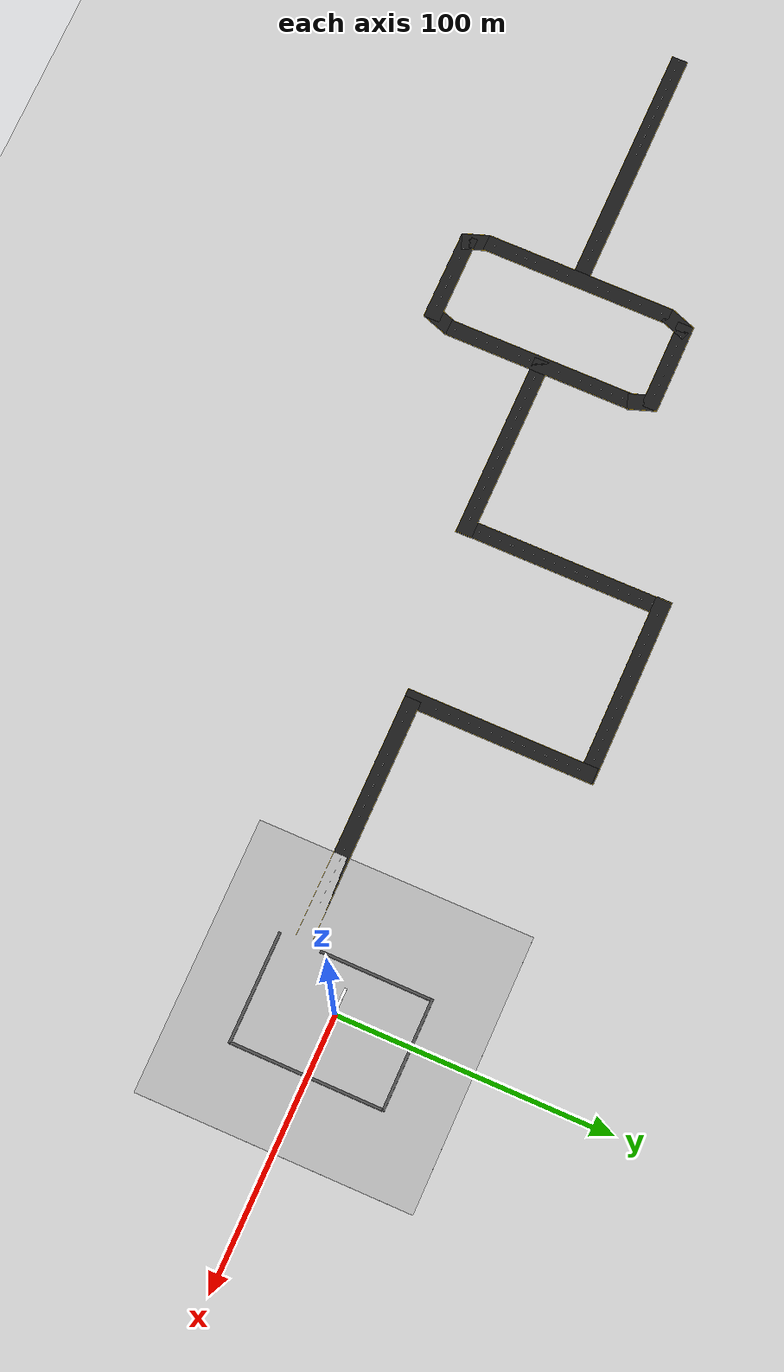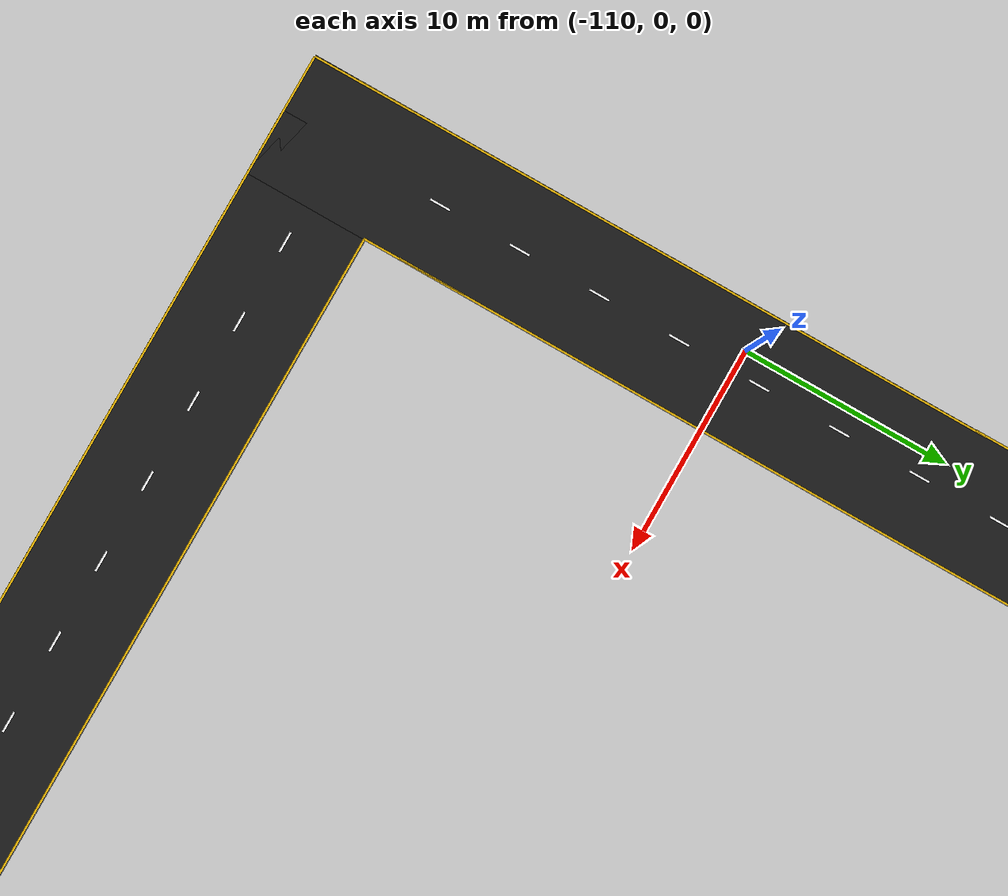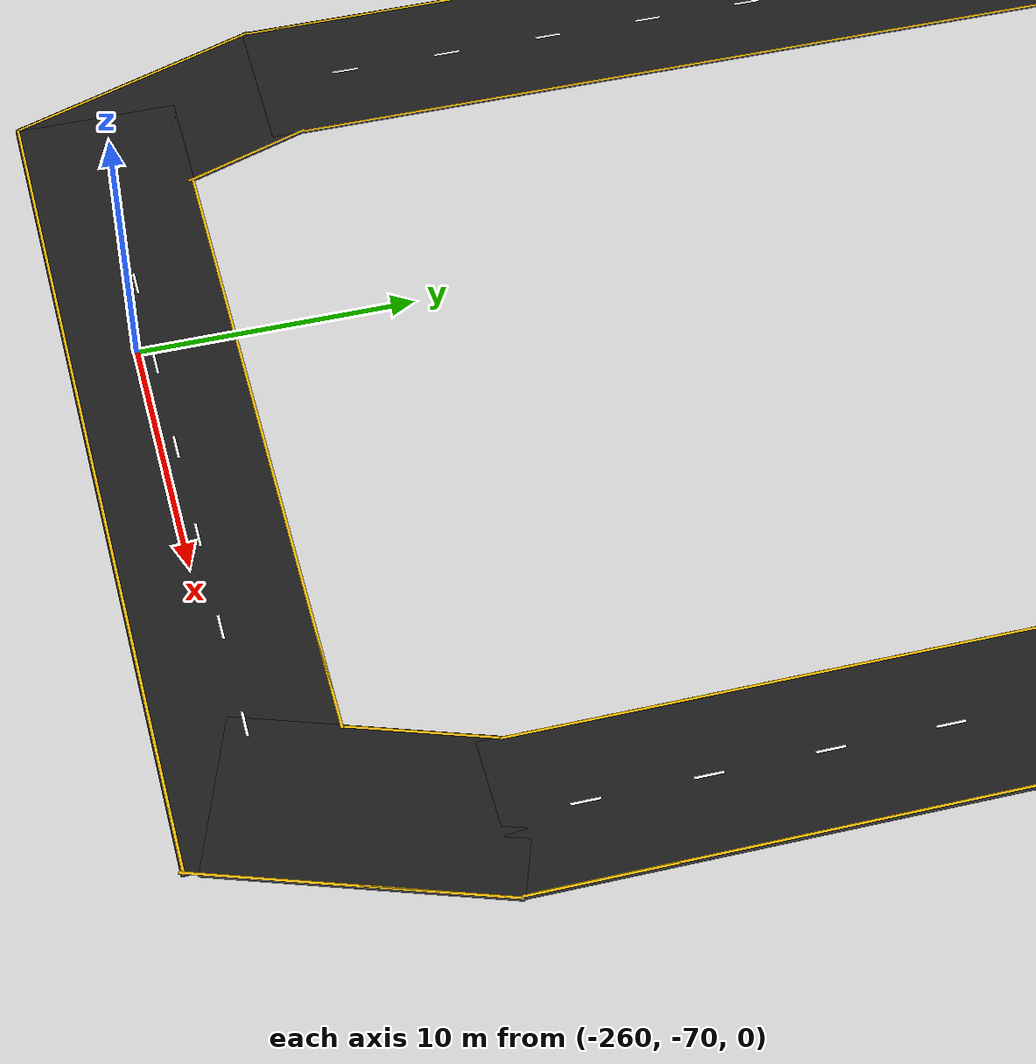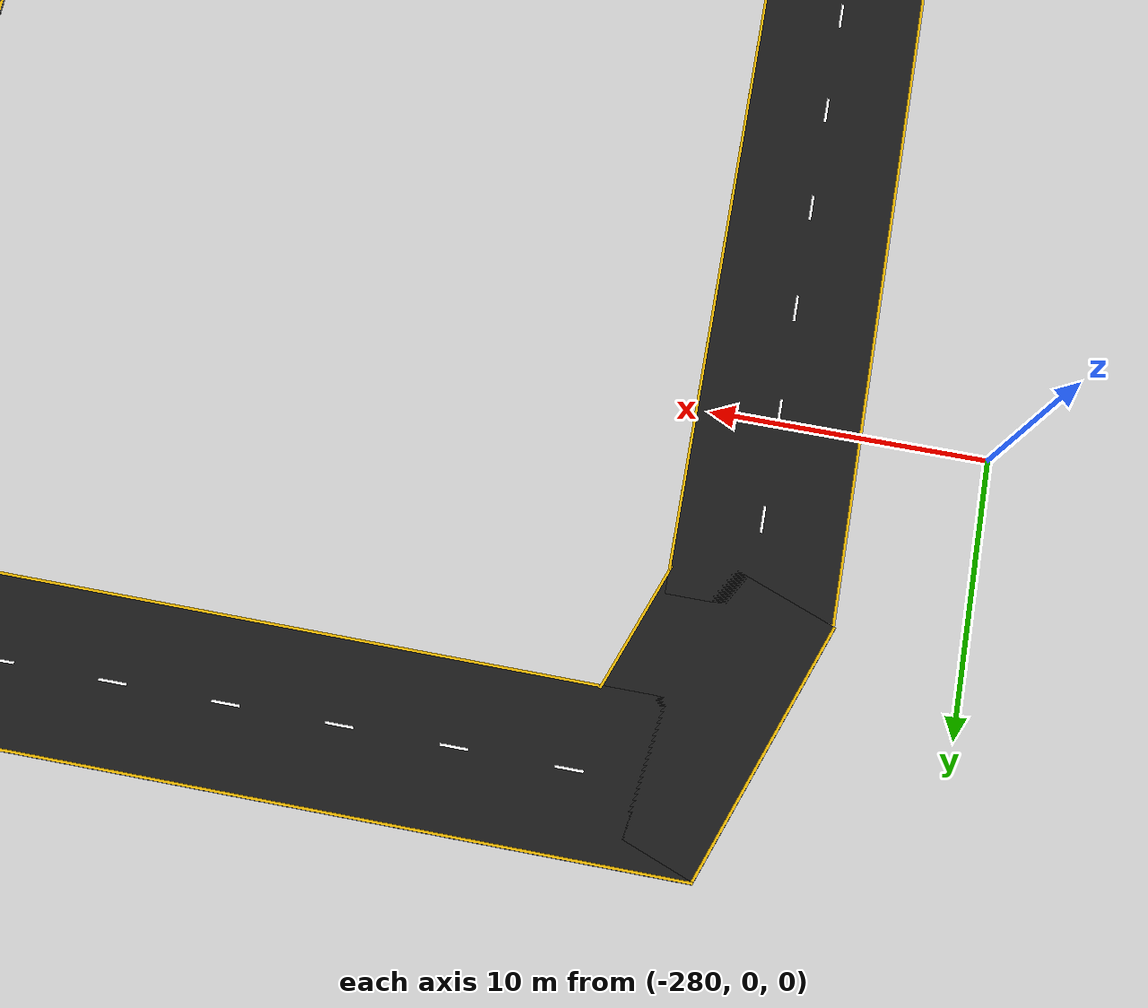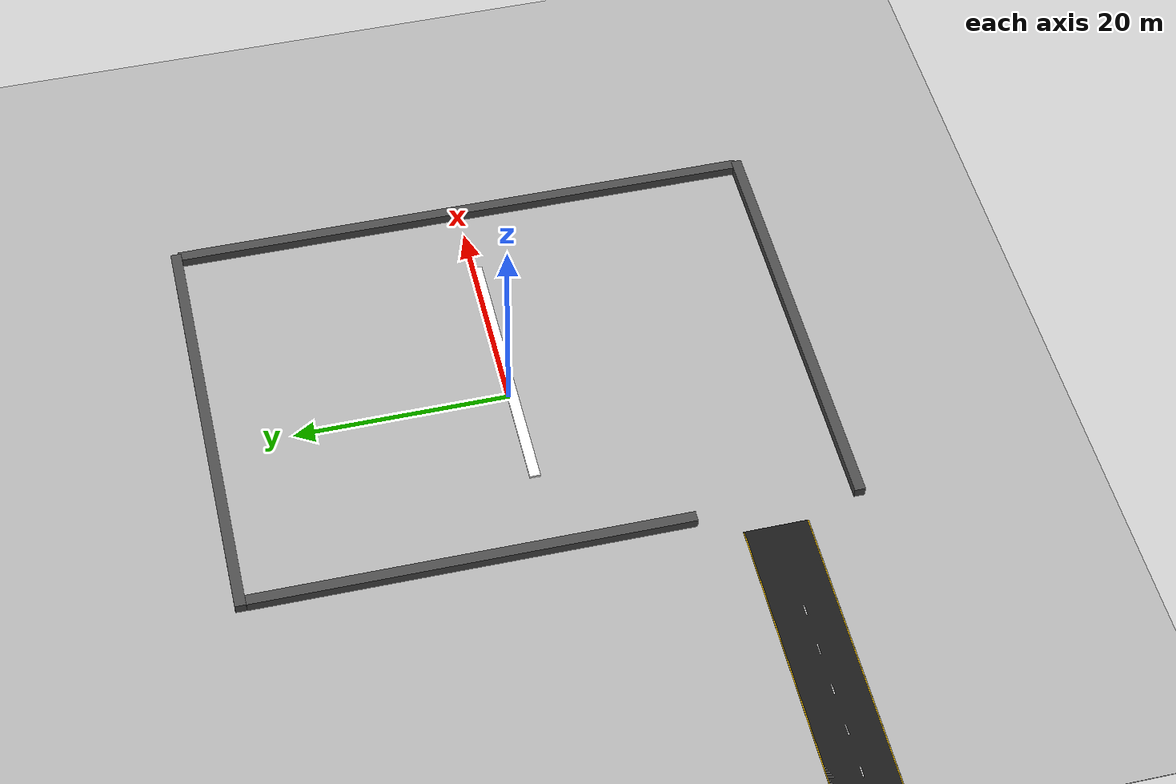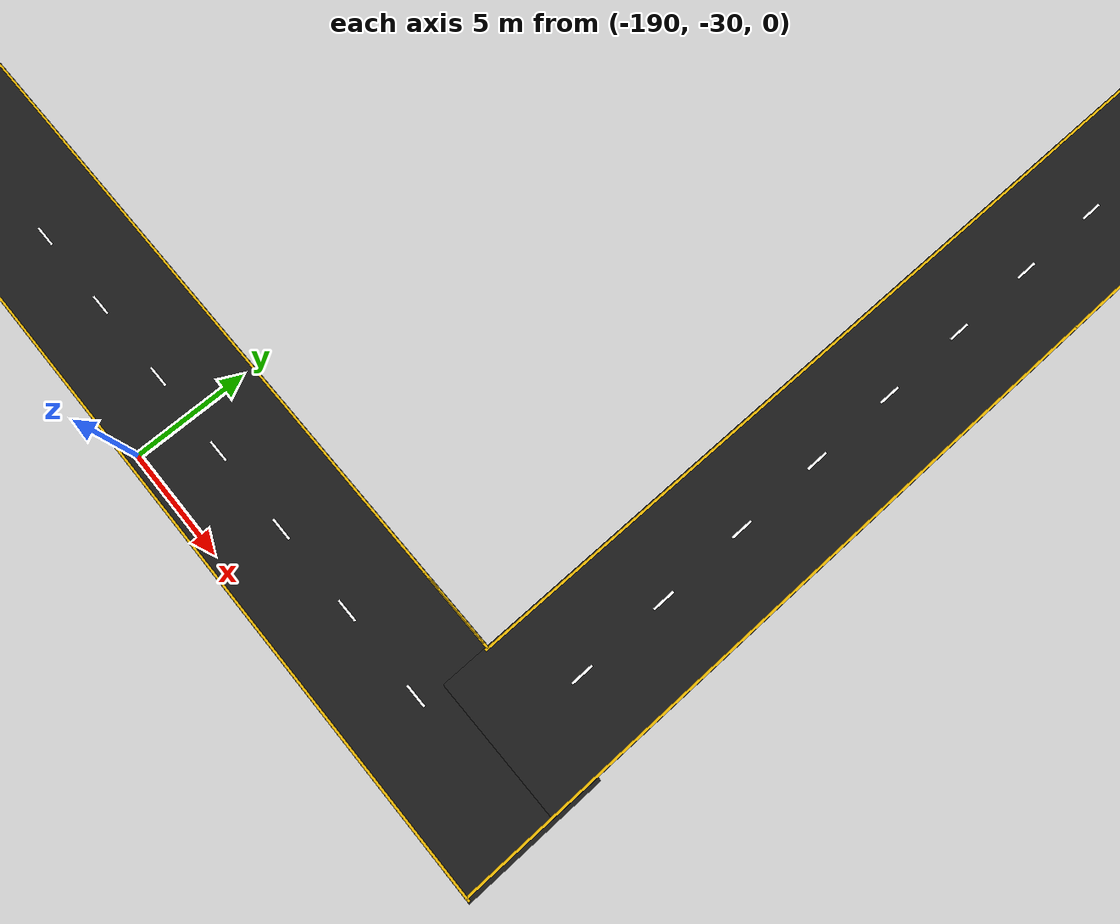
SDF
<?xml version="1.0"?>
<sdf version="1.8">
    <world name="parking_world">
        <physics name="1ms" type="ignored">
            <max_step_size>0.01</max_step_size>
            <real_time_factor>1.0</real_time_factor>
        </physics>

        <plugin
            filename="libignition-gazebo-physics-system.so"
            name="ignition::gazebo::systems::Physics">
        </plugin>

        <plugin
            filename="libignition-gazebo-user-commands-system.so"
            name="ignition::gazebo::systems::UserCommands">
        </plugin>

        <plugin
            filename="libignition-gazebo-scene-broadcaster-system.so"
            name="ignition::gazebo::systems::SceneBroadcaster">
        </plugin>

        <gravity>0 0 -9.8</gravity>
        <magnetic_field>5.565e-06 2.289e-05 -4.239e-05</magnetic_field>
        <atmosphere type='adiabatic' />

        <scene>
            <ambient>0.4 0.4 0.4 1</ambient>
            <background>0.7 0.7 0.7 1</background>
            <shadows>true</shadows>
        </scene>

        <model name='ground_plane'>
            <pose>0 0 0 0 0 0</pose>
            <self_collide>false</self_collide>
            <static>true</static>
            <link name='ground'>
                <pose>0 0 0 0 0 0</pose>
                <enable_wind>false</enable_wind>
                <visual name='visual'>
                    <geometry>
                        <plane>
                            <normal>0 0 1</normal>
                            <size>100 100</size>
                        </plane>
                    </geometry>
                    <material>
                        <ambient>0.8 0.8 0.8 1</ambient>
                        <diffuse>0.8 0.8 0.8 1</diffuse>
                        <specular>0.8 0.8 0.8 1</specular>
                        <emissive>0.0 0.0 0.0 1</emissive>
                    </material>
                </visual>
                <collision name='collision'>
                    <geometry>
                        <plane>
                            <normal>0 0 1</normal>
                            <size>100 100</size>
                        </plane>
                    </geometry>
                    <surface>
                        <friction>
                            <ode>
                            </ode>
                        </friction>
                        <bounce />
                        <contact />
                    </surface>
                </collision>
                <inertial>
                    <pose>0 0 0 0 0 0</pose>
                    <mass>1</mass>
                    <inertia>
                        <ixx>1</ixx>
                        <ixy>0</ixy>
                        <ixz>0</ixz>
                        <iyy>1</iyy>
                        <iyz>0</iyz>
                        <izz>1</izz>
                    </inertia>
                </inertial>
            </link>
        </model>

        <light type="directional" name="sun">
            <cast_shadows>true</cast_shadows>
            <pose>0 0 10 0 0 0</pose>
            <diffuse>0.8 0.8 0.8 1</diffuse>
            <specular>0.2 0.2 0.2 1</specular>
            <attenuation>
                <range>1000</range>
                <constant>0.9</constant>
                <linear>0.01</linear>
                <quadratic>0.001</quadratic>
            </attenuation>
            <direction>-0.5 0.1 -0.9</direction>
        </light>

        <include>
          <uri>/home/nat/ros2_parking/src/gz_proj/final_models/final_parking_lot</uri>
          <pose>0 0 0 0 0 0</pose>
        </include>

        <include>
          <uri>/home/nat/ros2_parking/src/gz_proj/final_models/final_roadway</uri>
          <pose>-360.7440 -27.5486 0 0 0 0</pose>
        </include>
    </world>
</sdf>

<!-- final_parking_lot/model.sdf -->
<sdf version="1.6">
  <model name="parking_model">
    <static>true</static> <!-- Static, since it represents a non-moving parking lot -->

    <link name="ground_plane">
      <pose>0 0 0 0 0 0</pose>
      <collision name="ground_plane_collision">
        <geometry>
          <plane>
            <normal>0 0 1</normal>
            <size>100 100</size>
          </plane>
        </geometry>
      </collision>
      <visual name="ground_plane_visual">
        <geometry>
          <plane>
            <normal>0 0 1</normal>
            <size>100 100</size>
          </plane>
        </geometry>
        <material>
          <ambient>0.4 0.4 0.4 1</ambient>
          <diffuse>0.7 0.7 0.7 1</diffuse>
        </material>
      </visual>
    </link>

    <!-- Box Models from parking_1.sdf -->
    <model name="box">
      <pose>2.7544 27.4405 0.5 0 0 0</pose>
      <link name="box_link">
        <collision name="box_collision">
          <geometry>
            <box>
              <size>40.5 1 1</size>
            </box>
          </geometry>
        </collision>
        <visual name="box_visual">
          <geometry>
            <box>
              <size>40.5 1 1</size>
            </box>
          </geometry>
          <material>
            <ambient>0.3 0.3 0.3 1</ambient>
            <diffuse>0.3 0.3 0.3 1</diffuse>
            <specular>1 1 1 1</specular>
          </material>
        </visual>
      </link>
    </model>

    <model name="box_1">
      <pose>2.55323 -27.9246 0.5 0 0 0</pose>
      <link name="box_1_link">
        <collision name="box_1_collision">
          <geometry>
            <box>
              <size>40.5 1 1</size>
            </box>
          </geometry>
        </collision>
        <visual name="box_1_visual">
          <geometry>
            <box>
              <size>40.5 1 1</size>
            </box>
          </geometry>
          <material>
            <ambient>0.3 0.3 0.3 1</ambient>
            <diffuse>0.3 0.3 0.3 1</diffuse>
            <specular>1 1 1 1</specular>
          </material>
        </visual>
      </link>
    </model>

    <model name="box_2">
      <pose>-17.1074 6.93047 0.5 0 0 -1.57509</pose>
      <link name="box_2_link">
        <collision name="box_2_collision">
          <geometry>
            <box>
              <size>40 1 1</size>
            </box>
          </geometry>
        </collision>
        <visual name="box_2_visual">
          <geometry>
            <box>
              <size>40 1 1</size>
            </box>
          </geometry>
          <material>
            <ambient>0.3 0.3 0.3 1</ambient>
            <diffuse>0.3 0.3 0.3 1</diffuse>
            <specular>1 1 1 1</specular>
          </material>
        </visual>
      </link>
    </model>

    <model name="box_3">
      <pose>22.5793 -0.265861 0.5 0 0 -1.57509</pose>
      <link name="box_3_link">
        <collision name="box_3_collision">
          <geometry>
            <box>
              <size>55 1 1</size>
            </box>
          </geometry>
        </collision>
        <visual name="box_3_visual">
          <geometry>
            <box>
              <size>55 1 1</size>
            </box>
          </geometry>
          <material>
            <ambient>0.3 0.3 0.3 1</ambient>
            <diffuse>0.3 0.3 0.3 1</diffuse>
            <specular>1 1 1 1</specular>
          </material>
        </visual>
      </link>
    </model>

    <include>
      <uri>/home/nat/ros2_parking/src/gz_proj/final_models/final_parking_lot/park_line</uri>
      <name>parking_line_1</name>
      <pose>-3.98234 24.9546 0 0 -0 0</pose>
    </include>
    <include>
      <uri>/home/nat/ros2_parking/src/gz_proj/final_models/final_parking_lot/park_line</uri>
      <name>parking_line_2</name>
      <pose>-1.73665 24.9465 0 0 -0 0</pose>
    </include>
    <include>
      <uri>/home/nat/ros2_parking/src/gz_proj/final_models/final_parking_lot/park_line</uri>
      <name>parking_line_3</name>
      <pose>0.482907 24.9396 0 0 -0 0</pose>
    </include>
    <include>
      <uri>/home/nat/ros2_parking/src/gz_proj/final_models/final_parking_lot/park_line</uri>
      <name>parking_line_4</name>
      <pose>2.71869 24.948 0 0 -0 0</pose>
    </include>
    <include>
      <uri>/home/nat/ros2_parking/src/gz_proj/final_models/final_parking_lot/park_line</uri>
      <name>parking_line_5</name>
      <pose>4.98036 24.95 0 0 -0 0</pose>
    </include>
    <include>
      <uri>/home/nat/ros2_parking/src/gz_proj/final_models/final_parking_lot/park_line</uri>
      <name>parking_line_6</name>
      <pose>-8.55096 24.9386 0 0 -0 0</pose>
    </include>
    <include>
      <uri>/home/nat/ros2_parking/src/gz_proj/final_models/final_parking_lot/park_line</uri>
      <name>parking_line_7</name>
      <pose>7.20404 24.9505 0 0 -0 0</pose>
    </include>
    <include>
      <uri>/home/nat/ros2_parking/src/gz_proj/final_models/final_parking_lot/park_line</uri>
      <name>parking_line_8</name>
      <pose>9.46097 24.9375 0 0 -0 0</pose>
    </include>
    <model name='box_0'>
      <pose>3.1681 -0.304853 0.018131 0 -0 0</pose>
      <link name='box_link'>
        <inertial>
          <inertia>
            <ixx>0.16666</ixx>
            <ixy>0</ixy>
            <ixz>0</ixz>
            <iyy>0.16666</iyy>
            <iyz>0</iyz>
            <izz>0.16666</izz>
          </inertia>
          <mass>1</mass>
          <pose>0 0 0 0 -0 0</pose>
        </inertial>
        <collision name='box_collision'>
          <geometry>
            <box>
              <size>25 1 0.5</size>
            </box>
          </geometry>
          <surface>
            <friction>
              <ode/>
            </friction>
            <bounce/>
            <contact/>
          </surface>
        </collision>
        <visual name='box_visual'>
          <geometry>
            <box>
              <size>25 1 0.5</size>
            </box>
          </geometry>
          <material>
            <ambient>0.3 0.3 0.3 1</ambient>
            <diffuse>1 1 1 1</diffuse>
            <specular>1 1 1 1</specular>
          </material>
        </visual>
        <pose>0 0 0 0 -0 0</pose>
        <enable_wind>false</enable_wind>
      </link>
      <static>false</static>
      <self_collide>false</self_collide>
    </model>
    <include>
      <uri>/home/nat/ros2_parking/src/gz_proj/final_models/final_parking_lot/park_line</uri>
      <name>parking_line_9</name>
      <pose>0.623859 2.2038 0 0 -0 0</pose>
    </include>
    <include>
      <uri>/home/nat/ros2_parking/src/gz_proj/final_models/final_parking_lot/park_line</uri>
      <name>parking_line_10</name>
      <pose>2.94336 2.18615 0 0 -0 0</pose>
    </include>
    <include>
      <uri>/home/nat/ros2_parking/src/gz_proj/final_models/final_parking_lot/park_line</uri>
      <name>parking_line_11</name>
      <pose>5.1725 2.25634 0.00639 0 -0 0</pose>
    </include>
    <include>
      <uri>/home/nat/ros2_parking/src/gz_proj/final_models/final_parking_lot/park_line</uri>
      <name>parking_line_12</name>
      <pose>7.49458 2.24335 0 0 -0 0</pose>
    </include>
    <include>
      <uri>/home/nat/ros2_parking/src/gz_proj/final_models/final_parking_lot/park_line</uri>
      <name>parking_line_13</name>
      <pose>9.6991 2.23042 0 0 -0 0</pose>
    </include>
    <include>
      <uri>/home/nat/ros2_parking/src/gz_proj/final_models/final_parking_lot/park_line</uri>
      <name>parking_line_14</name>
      <pose>12.1072 2.21746 0 0 -0 0</pose>
    </include>
    <include>
      <uri>/home/nat/ros2_parking/src/gz_proj/final_models/final_parking_lot/park_line</uri>
      <name>parking_line_15</name>
      <pose>14.3861 2.206 0 0 -0 0</pose>
    </include>
    <include>
      <uri>/home/nat/ros2_parking/src/gz_proj/final_models/final_parking_lot/park_line</uri>
      <name>parking_line_16</name>
      <pose>-1.62611 2.2114 0 0 -0 0</pose>
    </include>
    <include>
      <uri>/home/nat/ros2_parking/src/gz_proj/final_models/final_parking_lot/park_line</uri>
      <name>parking_line_17</name>
      <pose>-3.9054 2.1943 0 0 -0 0</pose>
    </include>
    <include>
      <uri>/home/nat/ros2_parking/src/gz_proj/final_models/final_parking_lot/park_line</uri>
      <name>parking_line_18</name>
      <pose>-6.1873 2.19921 0 0 -0 0</pose>
    </include>
    <include>
      <uri>/home/nat/ros2_parking/src/gz_proj/final_models/final_parking_lot/park_line</uri>
      <name>parking_line_19</name>
      <pose>-8.54946 2.21806 0 0 -0 0</pose>
    </include>
    <include>
      <uri>/home/nat/ros2_parking/src/gz_proj/final_models/final_parking_lot/park_line</uri>
      <name>parking_line_20</name>
      <pose>11.6148 24.9456 0 0 -0 0</pose>
    </include>
    <include>
      <uri>/home/nat/ros2_parking/src/gz_proj/final_models/final_parking_lot/park_line</uri>
      <name>parking_line_21</name>
      <pose>13.7867 24.9389 0 0 -0 0</pose>
    </include>
    <include>
      <uri>/home/nat/ros2_parking/src/gz_proj/final_models/final_parking_lot/park_line</uri>
      <name>parking_line_22</name>
      <pose>-8.59087 -2.80556 0 0 -0 0</pose>
    </include>
    <include>
      <uri>/home/nat/ros2_parking/src/gz_proj/final_models/final_parking_lot/park_line</uri>
      <name>parking_line_23</name>
      <pose>-6.18728 -25.4178 0 0 -0 0</pose>
    </include>
    <include>
      <uri>/home/nat/ros2_parking/src/gz_proj/final_models/final_parking_lot/park_line</uri>
      <name>parking_line_24</name>
      <pose>-3.90911 -2.81124 0 0 -0 0</pose>
    </include>
    <include>
      <uri>/home/nat/ros2_parking/src/gz_proj/final_models/final_parking_lot/park_line</uri>
      <name>parking_line_25</name>
      <pose>-1.64075 -2.78947 0 0 -0 0</pose>
    </include>
    <include>
      <uri>/home/nat/ros2_parking/src/gz_proj/final_models/final_parking_lot/park_line</uri>
      <name>parking_line_26</name>
      <pose>0.571282 -2.78826 0 0 -0 0</pose>
    </include>
    <include>
      <uri>/home/nat/ros2_parking/src/gz_proj/final_models/final_parking_lot/park_line</uri>
      <name>parking_line_27</name>
      <pose>2.90249 -2.79341 0 0 -0 0</pose>
    </include>
    <include>
      <uri>/home/nat/ros2_parking/src/gz_proj/final_models/final_parking_lot/park_line</uri>
      <name>parking_line_28</name>
      <pose>5.15332 -2.79715 0 0 -0 0</pose>
    </include>
    <include>
      <uri>/home/nat/ros2_parking/src/gz_proj/final_models/final_parking_lot/park_line</uri>
      <name>parking_line_29</name>
      <pose>7.38575 -2.79431 0 0 -0 0</pose>
    </include>
    <include>
      <uri>/home/nat/ros2_parking/src/gz_proj/final_models/final_parking_lot/park_line</uri>
      <name>parking_line_30</name>
      <pose>9.64515 -2.79826 0 0 -0 0</pose>
    </include>
    <include>
      <uri>/home/nat/ros2_parking/src/gz_proj/final_models/final_parking_lot/park_line</uri>
      <name>parking_line_31</name>
      <pose>11.9859 -2.80169 0 0 -0 0</pose>
    </include>
    <include>
      <uri>/home/nat/ros2_parking/src/gz_proj/final_models/final_parking_lot/park_line</uri>
      <name>parking_line_32</name>
      <pose>14.2605 -2.80072 0 0 -0 0</pose>
    </include>
    <include>
      <uri>/home/nat/ros2_parking/src/gz_proj/final_models/final_parking_lot/park_line</uri>
      <name>parking_line_33</name>
      <pose>-8.58724 -25.4181 0 0 -0 0</pose>
    </include>
    <include>
      <uri>/home/nat/ros2_parking/src/gz_proj/final_models/final_parking_lot/park_line</uri>
      <name>parking_line_34</name>
      <pose>-6.1889 -2.7994 0 0 -0 0</pose>
    </include>
    <include>
      <uri>/home/nat/ros2_parking/src/gz_proj/final_models/final_parking_lot/park_line</uri>
      <name>parking_line_35</name>
      <pose>-3.91731 -25.4271 0 0 -0 0</pose>
    </include>
    <include>
      <uri>/home/nat/ros2_parking/src/gz_proj/final_models/final_parking_lot/park_line</uri>
      <name>parking_line_36</name>
      <pose>-1.50304 -25.4212 0 0 -0 0</pose>
    </include>
    <include>
      <uri>/home/nat/ros2_parking/src/gz_proj/final_models/final_parking_lot/park_line</uri>
      <name>parking_line_37</name>
      <pose>0.820859 -25.4134 0 0 -0 0</pose>
    </include>
    <include>
      <uri>/home/nat/ros2_parking/src/gz_proj/final_models/final_parking_lot/park_line</uri>
      <name>parking_line_38</name>
      <pose>3.18759 -25.4205 0 0 -0 0</pose>
    </include>
    <include>
      <uri>/home/nat/ros2_parking/src/gz_proj/final_models/final_parking_lot/park_line</uri>
      <name>parking_line_39</name>
      <pose>5.59418 -25.42 0 0 -0 0</pose>
    </include>
    <include>
      <uri>/home/nat/ros2_parking/src/gz_proj/final_models/final_parking_lot/park_line</uri>
      <name>parking_line_40</name>
      <pose>7.93244 -25.4262 0 0 -0 0</pose>
    </include>
    <include>
      <uri>/home/nat/ros2_parking/src/gz_proj/final_models/final_parking_lot/park_line</uri>
      <name>parking_line_41</name>
      <pose>10.3479 -25.4209 0 0 -0 0</pose>
    </include>
    <include>
      <uri>/home/nat/ros2_parking/src/gz_proj/final_models/final_parking_lot/park_line</uri>
      <name>parking_line_42</name>
      <pose>12.7041 -25.4262 0 0 -0 0</pose>
    </include>
    <include>
      <uri>/home/nat/ros2_parking/src/gz_proj/final_models/final_parking_lot/park_line</uri>
      <name>parking_line_43</name>
      <pose>14.9309 -25.4037 0 0 -0 0</pose>
    </include>

  </model>
</sdf>

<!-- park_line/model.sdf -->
<sdf version="1.6">
  <model name="parking_line">
    <static>true</static>
    <link name="link">
      <visual name="visual">
        <geometry>
          <box>
            <size>0.1 4 0.05</size>   <!-- Adjust size to fit the parking lot -->
          </box>
        </geometry>
        <material>
          <script>
            <uri>/home/nat/gazebo_world/worlds/park_line/materials/scripts</uri>
            <name>ParkingLineMaterial</name>
            <uri>/home/nat/gazebo_world/worlds/park_line/materials/textures</uri>
          </script>
          <ambient> 1 1 1 1  </ambient>
          <diffuse> 1 1 1 1  </diffuse>
          <specular> 0.5 0.5 0.5 1 </specular>
          <emissive> 0 0 0 0 </emissive>
        </material>
      </visual>
      <collision name="collision">
        <geometry>
          <box>
            <size>0.1 4 0.05</size>
          </box>
        </geometry>
      </collision>
    </link>
  </model>
</sdf>

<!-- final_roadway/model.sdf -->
<sdf version="1.6">
  <model name="roadway_model">
    <static>true</static>
    <include>
      <uri>/home/nat/ros2_parking/src/gz_proj/final_models/final_roadway/road_model</uri>
      <name>road_1</name>
      <pose>40.259 0 0 0 -0 0</pose>
    </include>
    <include>
      <uri>/home/nat/ros2_parking/src/gz_proj/final_models/final_roadway/road_line_model</uri>
      <name>road_line_1</name>
      <pose>-4 0 0.05 0 -0 0</pose>
    </include>
    <include>
      <uri>/home/nat/ros2_parking/src/gz_proj/final_models/final_roadway/road_line_model</uri>
      <name>road_line_2</name>
      <pose>0 0 0.05 0 -0 0</pose>
    </include>
    <include>
      <uri>/home/nat/ros2_parking/src/gz_proj/final_models/final_roadway/road_line_model</uri>
      <name>road_line_3</name>
      <pose>4 0 0.05 0 -0 0</pose>
    </include>
    <include>
      <uri>/home/nat/ros2_parking/src/gz_proj/final_models/final_roadway/road_line_model</uri>
      <name>road_line_4</name>
      <pose>8 0 0.05 0 -0 0</pose>
    </include>
    <include>
      <uri>/home/nat/ros2_parking/src/gz_proj/final_models/final_roadway/road_line_model</uri>
      <name>road_line_5</name>
      <pose>12 0 0.05 0 -0 0</pose>
    </include>
    <include>
      <uri>/home/nat/ros2_parking/src/gz_proj/final_models/final_roadway/road_line_model</uri>
      <name>road_line_6</name>
      <pose>16 0 0.05 0 -0 0</pose>
    </include>
    <include>
      <uri>/home/nat/ros2_parking/src/gz_proj/final_models/final_roadway/road_line_model</uri>
      <name>road_line_7</name>
      <pose>20 0 0.05 0 -0 0</pose>
    </include>
    <include>
      <uri>/home/nat/ros2_parking/src/gz_proj/final_models/final_roadway/road_line_model</uri>
      <name>road_line_8</name>
      <pose>24 0 0.05 0 -0 0</pose>
    </include>
    <include>
      <uri>/home/nat/ros2_parking/src/gz_proj/final_models/final_roadway/road_line_model</uri>
      <name>road_line_9</name>
      <pose>28 0 0.05 0 -0 0</pose>
    </include>
    <include>
      <uri>/home/nat/ros2_parking/src/gz_proj/final_models/final_roadway/road_line_model</uri>
      <name>road_line_10</name>
      <pose>32 0 0.05 0 -0 0</pose>
    </include>
    <include>
      <uri>/home/nat/ros2_parking/src/gz_proj/final_models/final_roadway/road_line_model</uri>
      <name>road_line_11</name>
      <pose>36 0 0.05 0 -0 0</pose>
    </include>
    <include>
      <uri>/home/nat/ros2_parking/src/gz_proj/final_models/final_roadway/road_line_model</uri>
      <name>road_line_12</name>
      <pose>40 0 0.05 0 -0 0</pose>
    </include>
    <include>
      <uri>/home/nat/ros2_parking/src/gz_proj/final_models/final_roadway/road_line_model</uri>
      <name>road_line_13</name>
      <pose>44 0 0.05 0 -0 0</pose>
    </include>
    <include>
      <uri>/home/nat/ros2_parking/src/gz_proj/final_models/final_roadway/road_line_model</uri>
      <name>road_line_14</name>
      <pose>48 0 0.05 0 -0 0</pose>
    </include>
    <include>
      <uri>/home/nat/ros2_parking/src/gz_proj/final_models/final_roadway/road_line_model</uri>
      <name>road_line_15</name>
      <pose>52 0 0.05 0 -0 0</pose>
    </include>
    <include>
      <uri>/home/nat/ros2_parking/src/gz_proj/final_models/final_roadway/road_line_model</uri>
      <name>road_line_16</name>
      <pose>56 0 0.05 0 -0 0</pose>
    </include>
    <include>
      <uri>/home/nat/ros2_parking/src/gz_proj/final_models/final_roadway/road_line_model</uri>
      <name>road_line_17</name>
      <pose>60 0 0.05 0 -0 0</pose>
    </include>
    <include>
      <uri>/home/nat/ros2_parking/src/gz_proj/final_models/final_roadway/road_line_model</uri>
      <name>road_line_18</name>
      <pose>64 0 0.05 0 -0 0</pose>
    </include>
    <include>
      <uri>/home/nat/ros2_parking/src/gz_proj/final_models/final_roadway/road_line_model</uri>
      <name>road_line_19</name>
      <pose>68 0 0.05 0 -0 0</pose>
    </include>
    <include>
      <uri>/home/nat/ros2_parking/src/gz_proj/final_models/final_roadway/road_line_model</uri>
      <name>road_line_20</name>
      <pose>72 0 0.05 0 -0 0</pose>
    </include>
    <include>
      <uri>/home/nat/ros2_parking/src/gz_proj/final_models/final_roadway/road_line_model</uri>
      <name>road_line_21</name>
      <pose>76 0 0.05 0 -0 0</pose>
    </include>
    <include>
      <uri>/home/nat/ros2_parking/src/gz_proj/final_models/final_roadway/road_line_model</uri>
      <name>road_line_22</name>
      <pose>80 0 0.05 0 -0 0</pose>
    </include>
    <include>
      <uri>/home/nat/ros2_parking/src/gz_proj/final_models/final_roadway/road_model3</uri>
      <name>road_intersect</name>
      <pose>88.2455 -0.660589 0 0 -0 1.57</pose>
    </include>
    <include>
      <uri>/home/nat/ros2_parking/src/gz_proj/final_models/final_roadway/roadinter_model</uri>
      <name>road_intersect_turn</name>
      <pose>89.7815 38.078 0 0 -0 1.21297</pose>
    </include>
    <include>
      <uri>/home/nat/ros2_parking/src/gz_proj/final_models/final_roadway/roadinter_model</uri>
      <name>road_intersect_turn_1</name>
      <pose>121.719 37.6818 0 0 0 -1.23485</pose>
    </include>
    <include>
      <uri>/home/nat/ros2_parking/src/gz_proj/final_models/final_roadway/roadinter_model</uri>
      <name>road_intersect_turn_2</name>
      <pose>121.519 -38.6943 0 0 -0 1.2348</pose>
    </include>
    <include>
      <uri>/home/nat/ros2_parking/src/gz_proj/final_models/final_roadway/roadinter_model</uri>
      <name>road_intersect_turn_3</name>
      <pose>89.6622 -39.1968 0 0 0 -1.23485</pose>
    </include>
    <include>
      <uri>/home/nat/ros2_parking/src/gz_proj/final_models/final_roadway/road_model4</uri>
      <name>road_intersect_straight</name>
      <pose>105.579 -41.9238 0 0 -0 0</pose>
    </include>
    <include>
      <uri>/home/nat/ros2_parking/src/gz_proj/final_models/final_roadway/road_line_model</uri>
      <name>road_line_str_1</name>
      <pose>93.4718 -41.9238 0.05 0 -0 0</pose>
    </include>
    <include>
      <uri>/home/nat/ros2_parking/src/gz_proj/final_models/final_roadway/road_line_model</uri>
      <name>road_line_str_2</name>
      <pose>97.4718 -41.9238 0.05 0 -0 0</pose>
    </include>
    <include>
      <uri>/home/nat/ros2_parking/src/gz_proj/final_models/final_roadway/road_line_model</uri>
      <name>road_line_str_3</name>
      <pose>101.472 -41.9238 0.05 0 -0 0</pose>
    </include>
    <include>
      <uri>/home/nat/ros2_parking/src/gz_proj/final_models/final_roadway/road_line_model</uri>
      <name>road_line_str_4</name>
      <pose>105.472 -41.9238 0.05 0 -0 0</pose>
    </include>
    <include>
      <uri>/home/nat/ros2_parking/src/gz_proj/final_models/final_roadway/road_line_model</uri>
      <name>road_line_str_5</name>
      <pose>109.472 -41.9238 0.05 0 -0 0</pose>
    </include>
    <include>
      <uri>/home/nat/ros2_parking/src/gz_proj/final_models/final_roadway/road_line_model</uri>
      <name>road_line_str_6</name>
      <pose>113.472 -41.9238 0.05 0 -0 0</pose>
    </include>
    <include>
      <uri>/home/nat/ros2_parking/src/gz_proj/final_models/final_roadway/road_line_model</uri>
      <name>road_line_str_7</name>
      <pose>117.472 -41.9238 0.05 0 -0 0</pose>
    </include>
    <include>
      <uri>/home/nat/ros2_parking/src/gz_proj/final_models/final_roadway/road_model4</uri>
      <name>road_intersect_straight_1</name>
      <pose>105.782 40.885 0 0 -0 0</pose>
    </include>
    <include>
      <uri>/home/nat/ros2_parking/src/gz_proj/final_models/final_roadway/road_line_model</uri>
      <name>road_line_str1_1</name>
      <pose>93.4718 40.885 0.05 0 -0 0</pose>
    </include>
    <include>
      <uri>/home/nat/ros2_parking/src/gz_proj/final_models/final_roadway/road_line_model</uri>
      <name>road_line_str1_2</name>
      <pose>97.4718 40.885 0.05 0 -0 0</pose>
    </include>
    <include>
      <uri>/home/nat/ros2_parking/src/gz_proj/final_models/final_roadway/road_line_model</uri>
      <name>road_line_str1_3</name>
      <pose>101.472 40.885 0.05 0 -0 0</pose>
    </include>
    <include>
      <uri>/home/nat/ros2_parking/src/gz_proj/final_models/final_roadway/road_line_model</uri>
      <name>road_line_str1_4</name>
      <pose>105.472 40.885 0.05 0 -0 0</pose>
    </include>
    <include>
      <uri>/home/nat/ros2_parking/src/gz_proj/final_models/final_roadway/road_line_model</uri>
      <name>road_line_str1_5</name>
      <pose>109.472 40.885 0.05 0 -0 0</pose>
    </include>
    <include>
      <uri>/home/nat/ros2_parking/src/gz_proj/final_models/final_roadway/road_line_model</uri>
      <name>road_line_str1_6</name>
      <pose>113.472 40.885 0.05 0 -0 0</pose>
    </include>
    <include>
      <uri>/home/nat/ros2_parking/src/gz_proj/final_models/final_roadway/road_line_model</uri>
      <name>road_line_str1_7</name>
      <pose>117.472 40.885 0.05 0 -0 0</pose>
    </include>
    <include>
      <uri>/home/nat/ros2_parking/src/gz_proj/final_models/final_roadway/road_model3</uri>
      <name>road_intersect_1</name>
      <pose>122.973 -0.022883 0 0 -0 1.57</pose>
    </include>
    <include>
      <uri>/home/nat/ros2_parking/src/gz_proj/final_models/final_roadway/road_line_model</uri>
      <name>road_line_inter2_4</name>
      <pose>122.973 31.1058 0.05 0 -0 1.57</pose>
    </include>
    <include>
      <uri>/home/nat/ros2_parking/src/gz_proj/final_models/final_roadway/road_line_model</uri>
      <name>road_line_inter2_5</name>
      <pose>122.973 27.1058 0.05 0 -0 1.57</pose>
    </include>
    <include>
      <uri>/home/nat/ros2_parking/src/gz_proj/final_models/final_roadway/road_line_model</uri>
      <name>road_line_inter2_6</name>
      <pose>122.973 23.1058 0.05 0 -0 1.57</pose>
    </include>
    <include>
      <uri>/home/nat/ros2_parking/src/gz_proj/final_models/final_roadway/road_line_model</uri>
      <name>road_line_inter2_7</name>
      <pose>122.973 19.1058 0.05 0 -0 1.57</pose>
    </include>
    <include>
      <uri>/home/nat/ros2_parking/src/gz_proj/final_models/final_roadway/road_line_model</uri>
      <name>road_line_inter2_8</name>
      <pose>122.973 15.1058 0.05 0 -0 1.57</pose>
    </include>
    <include>
      <uri>/home/nat/ros2_parking/src/gz_proj/final_models/final_roadway/road_line_model</uri>
      <name>road_line_inter2_9</name>
      <pose>122.973 11.1058 0.05 0 -0 1.57</pose>
    </include>
    <include>
      <uri>/home/nat/ros2_parking/src/gz_proj/final_models/final_roadway/road_line_model</uri>
      <name>road_line_inter2_10</name>
      <pose>122.973 7.1058 0.05 0 -0 1.57</pose>
    </include>
    <include>
      <uri>/home/nat/ros2_parking/src/gz_proj/final_models/final_roadway/road_line_model</uri>
      <name>road_line_inter2_11</name>
      <pose>122.973 -4.24563 0.05 0 -0 1.57</pose>
    </include>
    <include>
      <uri>/home/nat/ros2_parking/src/gz_proj/final_models/final_roadway/road_line_model</uri>
      <name>road_line_inter2_12</name>
      <pose>122.973 -8.24563 0.05 0 -0 1.57</pose>
    </include>
    <include>
      <uri>/home/nat/ros2_parking/src/gz_proj/final_models/final_roadway/road_line_model</uri>
      <name>road_line_inter2_13</name>
      <pose>122.973 -12.2456 0.05 0 -0 1.57</pose>
    </include>
    <include>
      <uri>/home/nat/ros2_parking/src/gz_proj/final_models/final_roadway/road_line_model</uri>
      <name>road_line_inter2_14</name>
      <pose>122.973 -16.2456 0.05 0 -0 1.57</pose>
    </include>
    <include>
      <uri>/home/nat/ros2_parking/src/gz_proj/final_models/final_roadway/road_line_model</uri>
      <name>road_line_inter2_15</name>
      <pose>122.973 -20.2456 0.05 0 -0 1.57</pose>
    </include>
    <include>
      <uri>/home/nat/ros2_parking/src/gz_proj/final_models/final_roadway/road_line_model</uri>
      <name>road_line_inter2_16</name>
      <pose>122.973 -24.2456 0.05 0 -0 1.57</pose>
    </include>
    <include>
      <uri>/home/nat/ros2_parking/src/gz_proj/final_models/final_roadway/road_line_model</uri>
      <name>road_line_inter2_17</name>
      <pose>122.973 -28.2456 0.05 0 -0 1.57</pose>
    </include>
    <include>
      <uri>/home/nat/ros2_parking/src/gz_proj/final_models/final_roadway/road_line_model</uri>
      <name>road_line_inter2_18</name>
      <pose>122.973 -32.2456 0.05 0 -0 1.57</pose>
    </include>
    <include>
      <uri>/home/nat/ros2_parking/src/gz_proj/final_models/final_roadway/road_line_model</uri>
      <name>road_line_32</name>
      <pose>128.634 0 0.05 0 -0 0</pose>
    </include>
    <include>
      <uri>/home/nat/ros2_parking/src/gz_proj/final_models/final_roadway/road_line_model</uri>
      <name>road_line_33</name>
      <pose>132.634 0 0.05 0 -0 0</pose>
    </include>
    <include>
      <uri>/home/nat/ros2_parking/src/gz_proj/final_models/final_roadway/road_line_model</uri>
      <name>road_line_34</name>
      <pose>136.634 0 0.05 0 -0 0</pose>
    </include>
    <include>
      <uri>/home/nat/ros2_parking/src/gz_proj/final_models/final_roadway/road_line_model</uri>
      <name>road_line_35</name>
      <pose>140.634 0 0.05 0 -0 0</pose>
    </include>
    <include>
      <uri>/home/nat/ros2_parking/src/gz_proj/final_models/final_roadway/road_line_model</uri>
      <name>road_line_36</name>
      <pose>144.634 0 0.05 0 -0 0</pose>
    </include>
    <include>
      <uri>/home/nat/ros2_parking/src/gz_proj/final_models/final_roadway/road_line_model</uri>
      <name>road_line_37</name>
      <pose>148.634 0 0.05 0 -0 0</pose>
    </include>
    <include>
      <uri>/home/nat/ros2_parking/src/gz_proj/final_models/final_roadway/road_line_model</uri>
      <name>road_line_38</name>
      <pose>152.634 0 0.05 0 -0 0</pose>
    </include>
    <include>
      <uri>/home/nat/ros2_parking/src/gz_proj/final_models/final_roadway/road_line_model</uri>
      <name>road_line_39</name>
      <pose>156.634 0 0.05 0 -0 0</pose>
    </include>
    <include>
      <uri>/home/nat/ros2_parking/src/gz_proj/final_models/final_roadway/road_line_model</uri>
      <name>road_line_40</name>
      <pose>160.634 0 0.05 0 -0 0</pose>
    </include>
    <include>
      <uri>/home/nat/ros2_parking/src/gz_proj/final_models/final_roadway/road_line_model</uri>
      <name>road_line_41</name>
      <pose>164.634 0 0.05 0 -0 0</pose>
    </include>
    <include>
      <uri>/home/nat/ros2_parking/src/gz_proj/final_models/final_roadway/road_line_model</uri>
      <name>road_line_42</name>
      <pose>168.634 0 0.05 0 -0 0</pose>
    </include>
    <include>
      <uri>/home/nat/ros2_parking/src/gz_proj/final_models/final_roadway/road_line_model</uri>
      <name>road_line_43</name>
      <pose>172.634 0 0.05 0 -0 0</pose>
    </include>
    <include>
      <uri>/home/nat/ros2_parking/src/gz_proj/final_models/final_roadway/road_line_model</uri>
      <name>road_line_44</name>
      <pose>176.634 0 0.05 0 -0 0</pose>
    </include>
    <include>
      <uri>/home/nat/ros2_parking/src/gz_proj/final_models/final_roadway/road_line_model</uri>
      <name>road_line_45</name>
      <pose>180.634 0 0.05 0 -0 0</pose>
    </include>
    <include>
      <uri>/home/nat/ros2_parking/src/gz_proj/final_models/final_roadway/road_line_model</uri>
      <name>road_line_46</name>
      <pose>184.634 0 0.05 0 -0 0</pose>
    </include>
    <include>
      <uri>/home/nat/ros2_parking/src/gz_proj/final_models/final_roadway/road_line_model</uri>
      <name>road_line_inter4</name>
      <pose>88.2911 31.1058 0.05 0 -0 1.57</pose>
    </include>
    <include>
      <uri>/home/nat/ros2_parking/src/gz_proj/final_models/final_roadway/road_line_model</uri>
      <name>road_line_inter5</name>
      <pose>88.2911 27.1058 0.05 0 -0 1.57</pose>
    </include>
    <include>
      <uri>/home/nat/ros2_parking/src/gz_proj/final_models/final_roadway/road_line_model</uri>
      <name>road_line_inter6</name>
      <pose>88.2911 23.1058 0.05 0 -0 1.57</pose>
    </include>
    <include>
      <uri>/home/nat/ros2_parking/src/gz_proj/final_models/final_roadway/road_line_model</uri>
      <name>road_line_inter7</name>
      <pose>88.2911 19.1058 0.05 0 -0 1.57</pose>
    </include>
    <include>
      <uri>/home/nat/ros2_parking/src/gz_proj/final_models/final_roadway/road_line_model</uri>
      <name>road_line_inter8</name>
      <pose>88.2911 15.1058 0.05 0 -0 1.57</pose>
    </include>
    <include>
      <uri>/home/nat/ros2_parking/src/gz_proj/final_models/final_roadway/road_line_model</uri>
      <name>road_line_inter9</name>
      <pose>88.2911 11.1058 0.05 0 -0 1.57</pose>
    </include>
    <include>
      <uri>/home/nat/ros2_parking/src/gz_proj/final_models/final_roadway/road_line_model</uri>
      <name>road_line_inter10</name>
      <pose>88.2911 7.1058 0.05 0 -0 1.57</pose>
    </include>
    <include>
      <uri>/home/nat/ros2_parking/src/gz_proj/final_models/final_roadway/road_line_model</uri>
      <name>road_line_inter11</name>
      <pose>88.2911 -4.24563 0.05 0 -0 1.57</pose>
    </include>
    <include>
      <uri>/home/nat/ros2_parking/src/gz_proj/final_models/final_roadway/road_line_model</uri>
      <name>road_line_inter12</name>
      <pose>88.2911 -8.24563 0.05 0 -0 1.57</pose>
    </include>
    <include>
      <uri>/home/nat/ros2_parking/src/gz_proj/final_models/final_roadway/road_line_model</uri>
      <name>road_line_inter13</name>
      <pose>88.2911 -12.2456 0.05 0 -0 1.57</pose>
    </include>
    <include>
      <uri>/home/nat/ros2_parking/src/gz_proj/final_models/final_roadway/road_line_model</uri>
      <name>road_line_inter14</name>
      <pose>88.2911 -16.2456 0.05 0 -0 1.57</pose>
    </include>
    <include>
      <uri>/home/nat/ros2_parking/src/gz_proj/final_models/final_roadway/road_line_model</uri>
      <name>road_line_inter15</name>
      <pose>88.2911 -20.2456 0.05 0 -0 1.57</pose>
    </include>
    <include>
      <uri>/home/nat/ros2_parking/src/gz_proj/final_models/final_roadway/road_line_model</uri>
      <name>road_line_inter16</name>
      <pose>88.2911 -24.2456 0.05 0 -0 1.57</pose>
    </include>
    <include>
      <uri>/home/nat/ros2_parking/src/gz_proj/final_models/final_roadway/road_line_model</uri>
      <name>road_line_inter17</name>
      <pose>88.2911 -28.2456 0.05 0 -0 1.57</pose>
    </include>
    <include>
      <uri>/home/nat/ros2_parking/src/gz_proj/final_models/final_roadway/road_line_model</uri>
      <name>road_line_inter18</name>
      <pose>88.2911 -32.2456 0.05 0 -0 1.57</pose>
    </include>
    <include>
      <uri>/home/nat/ros2_parking/src/gz_proj/final_models/final_roadway/road_model3</uri>
      <name>road_3</name>
      <pose>187.996 35.9758 0 0 -0 1.57</pose>
    </include>
    <include>
      <uri>/home/nat/ros2_parking/src/gz_proj/final_models/final_roadway/road_line_model</uri>
      <name>road_line_47</name>
      <pose>187.996 4.9758 0.05 0 -0 1.57</pose>
    </include>
    <include>
      <uri>/home/nat/ros2_parking/src/gz_proj/final_models/final_roadway/road_line_model</uri>
      <name>road_line_48</name>
      <pose>187.996 8.9758 0.05 0 -0 1.57</pose>
    </include>
    <include>
      <uri>/home/nat/ros2_parking/src/gz_proj/final_models/final_roadway/road_line_model</uri>
      <name>road_line_49</name>
      <pose>187.996 12.9758 0.05 0 -0 1.57</pose>
    </include>
    <include>
      <uri>/home/nat/ros2_parking/src/gz_proj/final_models/final_roadway/road_line_model</uri>
      <name>road_line_50</name>
      <pose>187.996 16.9758 0.05 0 -0 1.57</pose>
    </include>
    <include>
      <uri>/home/nat/ros2_parking/src/gz_proj/final_models/final_roadway/road_line_model</uri>
      <name>road_line_51</name>
      <pose>187.996 20.9758 0.05 0 -0 1.57</pose>
    </include>
    <include>
      <uri>/home/nat/ros2_parking/src/gz_proj/final_models/final_roadway/road_line_model</uri>
      <name>road_line_52</name>
      <pose>187.996 24.9758 0.05 0 -0 1.57</pose>
    </include>
    <include>
      <uri>/home/nat/ros2_parking/src/gz_proj/final_models/final_roadway/road_line_model</uri>
      <name>road_line_53</name>
      <pose>187.996 28.9758 0.05 0 -0 1.57</pose>
    </include>
    <include>
      <uri>/home/nat/ros2_parking/src/gz_proj/final_models/final_roadway/road_line_model</uri>
      <name>road_line_54</name>
      <pose>187.996 32.9758 0.05 0 -0 1.57</pose>
    </include>
    <include>
      <uri>/home/nat/ros2_parking/src/gz_proj/final_models/final_roadway/road_line_model</uri>
      <name>road_line_55</name>
      <pose>187.996 36.9758 0.05 0 -0 1.57</pose>
    </include>
    <include>
      <uri>/home/nat/ros2_parking/src/gz_proj/final_models/final_roadway/road_line_model</uri>
      <name>road_line_56</name>
      <pose>187.996 40.9758 0.05 0 -0 1.57</pose>
    </include>
    <include>
      <uri>/home/nat/ros2_parking/src/gz_proj/final_models/final_roadway/road_line_model</uri>
      <name>road_line_57</name>
      <pose>187.996 44.9758 0.05 0 -0 1.57</pose>
    </include>
    <include>
      <uri>/home/nat/ros2_parking/src/gz_proj/final_models/final_roadway/road_line_model</uri>
      <name>road_line_58</name>
      <pose>187.996 48.9758 0.05 0 -0 1.57</pose>
    </include>
    <include>
      <uri>/home/nat/ros2_parking/src/gz_proj/final_models/final_roadway/road_line_model</uri>
      <name>road_line_59</name>
      <pose>187.996 52.9758 0.05 0 -0 1.57</pose>
    </include>
    <include>
      <uri>/home/nat/ros2_parking/src/gz_proj/final_models/final_roadway/road_line_model</uri>
      <name>road_line_60</name>
      <pose>187.996 56.9758 0.05 0 -0 1.57</pose>
    </include>
    <include>
      <uri>/home/nat/ros2_parking/src/gz_proj/final_models/final_roadway/road_line_model</uri>
      <name>road_line_61</name>
      <pose>187.996 60.9758 0.05 0 -0 1.57</pose>
    </include>
    <include>
      <uri>/home/nat/ros2_parking/src/gz_proj/final_models/final_roadway/road_line_model</uri>
      <name>road_line_62</name>
      <pose>187.996 64.9758 0.05 0 -0 1.57</pose>
    </include>
    <include>
      <uri>/home/nat/ros2_parking/src/gz_proj/final_models/final_roadway/road_line_model</uri>
      <name>road_line_63</name>
      <pose>187.996 68.9758 0.05 0 -0 1.57</pose>
    </include>
    <include>
      <uri>/home/nat/ros2_parking/src/gz_proj/final_models/final_roadway/road_model3</uri>
      <name>road_4</name>
      <pose>219.818 72.4253 0 0 -0 0</pose>
    </include>
    <include>
      <uri>/home/nat/ros2_parking/src/gz_proj/final_models/final_roadway/road_line_model</uri>
      <name>road_line_64</name>
      <pose>190.818 72.4253 0.05 0 -0 0</pose>
    </include>
    <include>
      <uri>/home/nat/ros2_parking/src/gz_proj/final_models/final_roadway/road_line_model</uri>
      <name>road_line_65</name>
      <pose>194.818 72.4253 0.05 0 -0 0</pose>
    </include>
    <include>
      <uri>/home/nat/ros2_parking/src/gz_proj/final_models/final_roadway/road_line_model</uri>
      <name>road_line_66</name>
      <pose>198.818 72.4253 0.05 0 -0 0</pose>
    </include>
    <include>
      <uri>/home/nat/ros2_parking/src/gz_proj/final_models/final_roadway/road_line_model</uri>
      <name>road_line_67</name>
      <pose>202.818 72.4253 0.05 0 -0 0</pose>
    </include>
    <include>
      <uri>/home/nat/ros2_parking/src/gz_proj/final_models/final_roadway/road_line_model</uri>
      <name>road_line_68</name>
      <pose>206.818 72.4253 0.05 0 -0 0</pose>
    </include>
    <include>
      <uri>/home/nat/ros2_parking/src/gz_proj/final_models/final_roadway/road_line_model</uri>
      <name>road_line_69</name>
      <pose>210.818 72.4253 0.05 0 -0 0</pose>
    </include>
    <include>
      <uri>/home/nat/ros2_parking/src/gz_proj/final_models/final_roadway/road_line_model</uri>
      <name>road_line_70</name>
      <pose>214.818 72.4253 0.05 0 -0 0</pose>
    </include>
    <include>
      <uri>/home/nat/ros2_parking/src/gz_proj/final_models/final_roadway/road_line_model</uri>
      <name>road_line_71</name>
      <pose>218.818 72.4253 0.05 0 -0 0</pose>
    </include>
    <include>
      <uri>/home/nat/ros2_parking/src/gz_proj/final_models/final_roadway/road_line_model</uri>
      <name>road_line_72</name>
      <pose>222.818 72.4253 0.05 0 -0 0</pose>
    </include>
    <include>
      <uri>/home/nat/ros2_parking/src/gz_proj/final_models/final_roadway/road_line_model</uri>
      <name>road_line_73</name>
      <pose>226.818 72.4253 0.05 0 -0 0</pose>
    </include>
    <include>
      <uri>/home/nat/ros2_parking/src/gz_proj/final_models/final_roadway/road_line_model</uri>
      <name>road_line_74</name>
      <pose>230.818 72.4253 0.05 0 -0 0</pose>
    </include>
    <include>
      <uri>/home/nat/ros2_parking/src/gz_proj/final_models/final_roadway/road_line_model</uri>
      <name>road_line_75</name>
      <pose>234.818 72.4253 0.05 0 -0 0</pose>
    </include>
    <include>
      <uri>/home/nat/ros2_parking/src/gz_proj/final_models/final_roadway/road_line_model</uri>
      <name>road_line_76</name>
      <pose>238.818 72.4253 0.05 0 -0 0</pose>
    </include>
    <include>
      <uri>/home/nat/ros2_parking/src/gz_proj/final_models/final_roadway/road_line_model</uri>
      <name>road_line_77</name>
      <pose>242.818 72.4253 0.05 0 -0 0</pose>
    </include>
    <include>
      <uri>/home/nat/ros2_parking/src/gz_proj/final_models/final_roadway/road_line_model</uri>
      <name>road_line_78</name>
      <pose>246.818 72.4253 0.05 0 -0 0</pose>
    </include>
    <include>
      <uri>/home/nat/ros2_parking/src/gz_proj/final_models/final_roadway/road_model3</uri>
      <name>road_5</name>
      <pose>251.8 39.8227 0 0 -0 1.57</pose>
    </include>
    <include>
      <uri>/home/nat/ros2_parking/src/gz_proj/final_models/final_roadway/road_line_model</uri>
      <name>road_line_79</name>
      <pose>251.8 68.8227 0.05 0 -0 1.57</pose>
    </include>
    <include>
      <uri>/home/nat/ros2_parking/src/gz_proj/final_models/final_roadway/road_line_model</uri>
      <name>road_line_80</name>
      <pose>251.8 64.8227 0.05 0 -0 1.57</pose>
    </include>
    <include>
      <uri>/home/nat/ros2_parking/src/gz_proj/final_models/final_roadway/road_line_model</uri>
      <name>road_line_81</name>
      <pose>251.8 60.8227 0.05 0 -0 1.57</pose>
    </include>
    <include>
      <uri>/home/nat/ros2_parking/src/gz_proj/final_models/final_roadway/road_line_model</uri>
      <name>road_line_82</name>
      <pose>251.8 56.8227 0.05 0 -0 1.57</pose>
    </include>
    <include>
      <uri>/home/nat/ros2_parking/src/gz_proj/final_models/final_roadway/road_line_model</uri>
      <name>road_line_83</name>
      <pose>251.8 52.8227 0.05 0 -0 1.57</pose>
    </include>
    <include>
      <uri>/home/nat/ros2_parking/src/gz_proj/final_models/final_roadway/road_line_model</uri>
      <name>road_line_84</name>
      <pose>251.8 48.8227 0.05 0 -0 1.57</pose>
    </include>
    <include>
      <uri>/home/nat/ros2_parking/src/gz_proj/final_models/final_roadway/road_line_model</uri>
      <name>road_line_85</name>
      <pose>251.8 44.8227 0.05 0 -0 1.57</pose>
    </include>
    <include>
      <uri>/home/nat/ros2_parking/src/gz_proj/final_models/final_roadway/road_line_model</uri>
      <name>road_line_86</name>
      <pose>251.8 40.8227 0.05 0 -0 1.57</pose>
    </include>
    <include>
      <uri>/home/nat/ros2_parking/src/gz_proj/final_models/final_roadway/road_line_model</uri>
      <name>road_line_87</name>
      <pose>251.8 36.8227 0.05 0 -0 1.57</pose>
    </include>
    <include>
      <uri>/home/nat/ros2_parking/src/gz_proj/final_models/final_roadway/road_line_model</uri>
      <name>road_line_88</name>
      <pose>251.8 32.8227 0.05 0 -0 1.57</pose>
    </include>
    <include>
      <uri>/home/nat/ros2_parking/src/gz_proj/final_models/final_roadway/road_line_model</uri>
      <name>road_line_89</name>
      <pose>251.8 28.8227 0.05 0 -0 1.57</pose>
    </include>
    <include>
      <uri>/home/nat/ros2_parking/src/gz_proj/final_models/final_roadway/road_line_model</uri>
      <name>road_line_90</name>
      <pose>251.8 24.8227 0.05 0 -0 1.57</pose>
    </include>
    <include>
      <uri>/home/nat/ros2_parking/src/gz_proj/final_models/final_roadway/road_line_model</uri>
      <name>road_line_91</name>
      <pose>251.8 20.8227 0.05 0 -0 1.57</pose>
    </include>
    <include>
      <uri>/home/nat/ros2_parking/src/gz_proj/final_models/final_roadway/road_line_model</uri>
      <name>road_line_92</name>
      <pose>251.8 16.8227 0.05 0 -0 1.57</pose>
    </include>
    <include>
      <uri>/home/nat/ros2_parking/src/gz_proj/final_models/final_roadway/road_line_model</uri>
      <name>road_line_93</name>
      <pose>251.8 12.8227 0.05 0 -0 1.57</pose>
    </include>
    <include>
      <uri>/home/nat/ros2_parking/src/gz_proj/final_models/final_roadway/road_model</uri>
      <name>road_6</name>
      <pose>296.578 7.75504 0 0 -0 0</pose>
    </include>
    <include>
      <uri>/home/nat/ros2_parking/src/gz_proj/final_models/final_roadway/road_line_model</uri>
      <name>road_line_94</name>
      <pose>256.578 7.75504 0.05 0 -0 0</pose>
    </include>
    <include>
      <uri>/home/nat/ros2_parking/src/gz_proj/final_models/final_roadway/road_line_model</uri>
      <name>road_line_95</name>
      <pose>260.578 7.75504 0.05 0 -0 0</pose>
    </include>
    <include>
      <uri>/home/nat/ros2_parking/src/gz_proj/final_models/final_roadway/road_line_model</uri>
      <name>road_line_96</name>
      <pose>264.578 7.75504 0.05 0 -0 0</pose>
    </include>
    <include>
      <uri>/home/nat/ros2_parking/src/gz_proj/final_models/final_roadway/road_line_model</uri>
      <name>road_line_97</name>
      <pose>268.578 7.75504 0.05 0 -0 0</pose>
    </include>
    <include>
      <uri>/home/nat/ros2_parking/src/gz_proj/final_models/final_roadway/road_line_model</uri>
      <name>road_line_98</name>
      <pose>272.578 7.75504 0.05 0 -0 0</pose>
    </include>
    <include>
      <uri>/home/nat/ros2_parking/src/gz_proj/final_models/final_roadway/road_line_model</uri>
      <name>road_line_99</name>
      <pose>276.578 7.75504 0.05 0 -0 0</pose>
    </include>
    <include>
      <uri>/home/nat/ros2_parking/src/gz_proj/final_models/final_roadway/road_line_model</uri>
      <name>road_line_100</name>
      <pose>280.578 7.75504 0.05 0 -0 0</pose>
    </include>
    <include>
      <uri>/home/nat/ros2_parking/src/gz_proj/final_models/final_roadway/road_line_model</uri>
      <name>road_line_101</name>
      <pose>284.578 7.75504 0.05 0 -0 0</pose>
    </include>
    <include>
      <uri>/home/nat/ros2_parking/src/gz_proj/final_models/final_roadway/road_line_model</uri>
      <name>road_line_102</name>
      <pose>288.578 7.75504 0.05 0 -0 0</pose>
    </include>
    <include>
      <uri>/home/nat/ros2_parking/src/gz_proj/final_models/final_roadway/road_line_model</uri>
      <name>road_line_103</name>
      <pose>292.578 7.75504 0.05 0 -0 0</pose>
    </include>
    <include>
      <uri>/home/nat/ros2_parking/src/gz_proj/final_models/final_roadway/road_line_model</uri>
      <name>road_line_104</name>
      <pose>296.578 7.75504 0.05 0 -0 0</pose>
    </include>
    <include>
      <uri>/home/nat/ros2_parking/src/gz_proj/final_models/final_roadway/road_line_model</uri>
      <name>road_line_105</name>
      <pose>300.578 7.75504 0.05 0 -0 0</pose>
    </include>
    <include>
      <uri>/home/nat/ros2_parking/src/gz_proj/final_models/final_roadway/road_line_model</uri>
      <name>road_line_106</name>
      <pose>304.578 7.75504 0.05 0 -0 0</pose>
    </include>
    <include>
      <uri>/home/nat/ros2_parking/src/gz_proj/final_models/final_roadway/road_line_model</uri>
      <name>road_line_107</name>
      <pose>308.578 7.75504 0.05 0 -0 0</pose>
    </include>
    <include>
      <uri>/home/nat/ros2_parking/src/gz_proj/final_models/final_roadway/road_line_model</uri>
      <name>road_line_108</name>
      <pose>312.578 7.75504 0.05 0 -0 0</pose>
    </include>
    <include>
      <uri>/home/nat/ros2_parking/src/gz_proj/final_models/final_roadway/road_line_model</uri>
      <name>road_line_109</name>
      <pose>316.578 7.75504 0.05 0 -0 0</pose>
    </include>
    <include>
      <uri>/home/nat/ros2_parking/src/gz_proj/final_models/final_roadway/road_line_model</uri>
      <name>road_line_110</name>
      <pose>320.578 7.75504 0.05 0 -0 0</pose>
    </include>
    <include>
      <uri>/home/nat/ros2_parking/src/gz_proj/final_models/final_roadway/road_line_model</uri>
      <name>road_line_111</name>
      <pose>324.578 7.75504 0.05 0 -0 0</pose>
    </include>
    <include>
      <uri>/home/nat/ros2_parking/src/gz_proj/final_models/final_roadway/road_line_model</uri>
      <name>road_line_112</name>
      <pose>328.578 7.75504 0.05 0 -0 0</pose>
    </include>
    <include>
      <uri>/home/nat/ros2_parking/src/gz_proj/final_models/final_roadway/road_line_model</uri>
      <name>road_line_113</name>
      <pose>332.578 7.75504 0.05 0 -0 0</pose>
    </include>
    <include>
      <uri>/home/nat/ros2_parking/src/gz_proj/final_models/final_roadway/road_model3</uri>
      <name>road_2</name>
      <pose>156.118 0.0783 0 0 -0 0</pose>
    </include>
    <include>
      <uri>/home/nat/ros2_parking/src/gz_proj/final_models/final_roadway/yellow_line_model</uri>
      <name>yellow_line_0</name>
      <pose>40.2513 2.94638 0.05 0 -0 0</pose>
    </include>
    <include>
      <uri>/home/nat/ros2_parking/src/gz_proj/final_models/final_roadway/yellow_line_model</uri>
      <name>yellow_line_1</name>
      <pose>40.2513 -2.94638 0.05 0 -0 0</pose>
    </include>
    <include>
      <uri>/home/nat/ros2_parking/src/gz_proj/final_models/final_roadway/yellow_line_model_2</uri>
      <name>yellow_line_2</name>
      <pose>85.3114 18.6527 0.05 0 -0 1.57</pose>
    </include>
    <include>
      <uri>/home/nat/ros2_parking/src/gz_proj/final_models/final_roadway/yellow_line_model_2</uri>
      <name>yellow_line_3</name>
      <pose>85.3116 -18.6038 0.05 0 -0 1.57</pose>
    </include>
    <include>
      <uri>/home/nat/ros2_parking/src/gz_proj/final_models/final_roadway/yellow_line_model_4</uri>
      <name>yellow_line_4</name>
      <pose>91.2221 -0.473941 0.05 0 -0 1.57</pose>
    </include>
    <include>
      <uri>/home/nat/ros2_parking/src/gz_proj/final_models/final_roadway/yellow_line_model_4</uri>
      <name>yellow_line_4_1</name>
      <pose>120.03 -0.253313 0.05 0 -0 1.57</pose>
    </include>
    <include>
      <uri>/home/nat/ros2_parking/src/gz_proj/final_models/final_roadway/yellow_line_model_2</uri>
      <name>yellow_line_2_1</name>
      <pose>125.886 18.6792 0.05 0 -0 1.57</pose>
    </include>
    <include>
      <uri>/home/nat/ros2_parking/src/gz_proj/final_models/final_roadway/yellow_line_model_2</uri>
      <name>yellow_line_2_2</name>
      <pose>125.866 -18.8015 0.05 0 -0 1.57</pose>
    </include>
    <include>
      <uri>/home/nat/ros2_parking/src/gz_proj/final_models/final_roadway/yellow_line_model_2</uri>
      <name>yellow_line_2_1_1</name>
      <pose>104.489 43.828 0.05 0 -0 0</pose>
    </include>
    <include>
      <uri>/home/nat/ros2_parking/src/gz_proj/final_models/final_roadway/yellow_line_model_2</uri>
      <name>yellow_line_2_1_2</name>
      <pose>104.306 -44.8272 0.05 0 -0 0</pose>
    </include>
    <include>
      <uri>/home/nat/ros2_parking/src/gz_proj/final_models/final_roadway/yellow_line_model_3</uri>
      <name>yellow_line_2_1_3</name>
      <pose>105.234 -38.9666 0.05 0 -0 0</pose>
    </include>
    <include>
      <uri>/home/nat/ros2_parking/src/gz_proj/final_models/final_roadway/yellow_line_model_3</uri>
      <name>yellow_line_2_1_4</name>
      <pose>105.448 37.918 0.05 0 -0 0</pose>
    </include>
    <include>
      <uri>/home/nat/ros2_parking/src/gz_proj/final_models/final_roadway/yellow_line_model_turn</uri>
      <name>yellow_line_2_1_5</name>
      <pose>87.025 39.1087 0.05 0 -0 1.21297</pose>
    </include>
    <include>
      <uri>/home/nat/ros2_parking/src/gz_proj/final_models/final_roadway/yellow_line_model_turn</uri>
      <name>yellow_line_2_1_5_1</name>
      <pose>124.09 -40.2531 0.05 0 -0 1.2348</pose>
    </include>
    <include>
      <uri>/home/nat/ros2_parking/src/gz_proj/final_models/final_roadway/yellow_line_model_turn</uri>
      <name>yellow_line_2_1_5_1_1</name>
      <pose>124.31 39.1073 0.05 0 0 -1.2348</pose>
    </include>
    <include>
      <uri>/home/nat/ros2_parking/src/gz_proj/final_models/final_roadway/yellow_line_model_turn</uri>
      <name>yellow_line_2_1_5_1_2</name>
      <pose>86.9124 -40.1604 0.05 0 0 -1.2348</pose>
    </include>
    <include>
      <uri>/home/nat/ros2_parking/src/gz_proj/final_models/final_roadway/yellow_line_model_short</uri>
      <name>yellow_line_2_1_5_1_3</name>
      <pose>91.9429 -36.7679 0.05 0 0 -1.2348</pose>
    </include>
    <include>
      <uri>/home/nat/ros2_parking/src/gz_proj/final_models/final_roadway/yellow_line_model_short</uri>
      <name>yellow_line_2_1_5_1_3_1</name>
      <pose>119.299 35.6789 0.05 0 0 -1.2348</pose>
    </include>
    <include>
      <uri>/home/nat/ros2_parking/src/gz_proj/final_models/final_roadway/yellow_line_model_short</uri>
      <name>yellow_line_2_1_5_1_3_2</name>
      <pose>119.155 -36.5739 0.05 0 -0 1.2348</pose>
    </include>
    <include>
      <uri>/home/nat/ros2_parking/src/gz_proj/final_models/final_roadway/yellow_line_model_short</uri>
      <name>yellow_line_2_1_5_1_3_2_1</name>
      <pose>125.104 -37.3497 0.05 0 -0 1.2348</pose>
    </include>
    <include>
      <uri>/home/nat/ros2_parking/src/gz_proj/final_models/final_roadway/yellow_line_model_short</uri>
      <name>yellow_line_2_1_5_1_3_2_2</name>
      <pose>92.0529 35.6666 0.05 0 -0 1.213</pose>
    </include>
    <include>
      <uri>/home/nat/ros2_parking/src/gz_proj/final_models/final_roadway/yellow_line_model_2</uri>
      <name>yellow_line_2_2_1</name>
      <pose>141.695 -2.86628 0.05 0 -0 0</pose>
    </include>
    <include>
      <uri>/home/nat/ros2_parking/src/gz_proj/final_models/final_roadway/yellow_line_model_2</uri>
      <name>yellow_line_2_2_1_1</name>
      <pose>175.315 -2.867 0.05 0 -0 0</pose>
    </include>
    <include>
      <uri>/home/nat/ros2_parking/src/gz_proj/final_models/final_roadway/yellow_line_model_2</uri>
      <name>yellow_line_2_2_1_2</name>
      <pose>169.082 3.01868 0.05 0 -0 0</pose>
    </include>
    <include>
      <uri>/home/nat/ros2_parking/src/gz_proj/final_models/final_roadway/yellow_line_model_2</uri>
      <name>yellow_line_2_2_1_3</name>
      <pose>141.574 3.0187 0.05 0 -0 0</pose>
    </include>
    <include>
      <uri>/home/nat/ros2_parking/src/gz_proj/final_models/final_roadway/yellow_line_model_2</uri>
      <name>yellow_line_2_1_6</name>
      <pose>185.071 18.6348 0.05 0 -0 1.57</pose>
    </include>
    <include>
      <uri>/home/nat/ros2_parking/src/gz_proj/final_models/final_roadway/yellow_line_model_short</uri>
      <name>yellow_line_2_1_5_1_3_2_3</name>
      <pose>157.445 -2.867 0.05 0 -0 0</pose>
    </include>
    <include>
      <uri>/home/nat/ros2_parking/src/gz_proj/final_models/final_roadway/yellow_line_model_2</uri>
      <name>yellow_line_2_1_6_1</name>
      <pose>185.086 50.0546 0.05 0 -0 1.57</pose>
    </include>
    <include>
      <uri>/home/nat/ros2_parking/src/gz_proj/final_models/final_roadway/yellow_line_model_2</uri>
      <name>yellow_line_2_1_6_2</name>
      <pose>190.917 12.86 0.05 0 -0 1.57</pose>
    </include>
    <include>
      <uri>/home/nat/ros2_parking/src/gz_proj/final_models/final_roadway/yellow_line_model_2</uri>
      <name>yellow_line_2_1_6_3</name>
      <pose>190.945 44.2299 0.05 0 -0 1.57</pose>
    </include>
    <include>
      <uri>/home/nat/ros2_parking/src/gz_proj/final_models/final_roadway/yellow_line_model_turn</uri>
      <name>yellow_line_2_1_5_1_1_1</name>
      <pose>190.946 64.4166 0.05 0 0 -1.57</pose>
    </include>
    <include>
      <uri>/home/nat/ros2_parking/src/gz_proj/final_models/final_roadway/yellow_line_model_turn</uri>
      <name>yellow_line_2_1_5_1_1_1_1</name>
      <pose>185.086 70.4372 0.05 0 0 -1.57</pose>
    </include>
    <include>
      <uri>/home/nat/ros2_parking/src/gz_proj/final_models/final_roadway/yellow_line_model_4</uri>
      <name>yellow_line_4_1_1</name>
      <pose>219.086 75.3712 0.05 0 -0 0</pose>
    </include>
    <include>
      <uri>/home/nat/ros2_parking/src/gz_proj/final_models/final_roadway/yellow_line_model_4</uri>
      <name>yellow_line_4_1_1_1</name>
      <pose>282.866 4.81012 0.05 0 -0 0</pose>
    </include>
    <include>
      <uri>/home/nat/ros2_parking/src/gz_proj/final_models/final_roadway/yellow_line_model_2</uri>
      <name>yellow_line_2_2_1_2_1</name>
      <pose>206.636 69.4848 0.05 0 -0 0</pose>
    </include>
    <include>
      <uri>/home/nat/ros2_parking/src/gz_proj/final_models/final_roadway/yellow_line_model_2</uri>
      <name>yellow_line_2_2_1_2_1_1</name>
      <pose>233.02 69.4848 0.05 0 -0 0</pose>
    </include>
    <include>
      <uri>/home/nat/ros2_parking/src/gz_proj/final_models/final_roadway/yellow_line_model_2</uri>
      <name>yellow_line_2_1_6_3_1</name>
      <pose>254.76 59.6639 0.05 0 -0 1.57</pose>
    </include>
    <include>
      <uri>/home/nat/ros2_parking/src/gz_proj/final_models/final_roadway/yellow_line_model_2</uri>
      <name>yellow_line_2_1_6_3_1_1</name>
      <pose>254.74 28.2107 0.05 0 -0 1.57</pose>
    </include>
    <include>
      <uri>/home/nat/ros2_parking/src/gz_proj/final_models/final_roadway/yellow_line_model_2</uri>
      <name>yellow_line_2_1_6_3_1_2</name>
      <pose>248.846 53.7357 0.05 0 -0 1.57</pose>
    </include>
    <include>
      <uri>/home/nat/ros2_parking/src/gz_proj/final_models/final_roadway/yellow_line_model_2</uri>
      <name>yellow_line_2_1_6_3_1_3</name>
      <pose>248.846 22.7876 0.05 0 -0 1.57</pose>
    </include>
    <include>
      <uri>/home/nat/ros2_parking/src/gz_proj/final_models/final_roadway/yellow_line_model_4</uri>
      <name>yellow_line_4_1_1_1_1</name>
      <pose>288.696 10.6904 0.05 0 -0 0</pose>
    </include>
    <include>
      <uri>/home/nat/ros2_parking/src/gz_proj/final_models/final_roadway/yellow_line_model_2</uri>
      <name>yellow_line_2_2_1_2_1_1_1</name>
      <pose>325.77 4.8101 0.05 0 -0 0</pose>
    </include>
    <include>
      <uri>/home/nat/ros2_parking/src/gz_proj/final_models/final_roadway/yellow_line_model_2</uri>
      <name>yellow_line_2_2_1_2_1_1_2</name>
      <pose>325.698 10.6904 0.05 0 -0 0</pose>
    </include>
    <include>
      <uri>/home/nat/ros2_parking/src/gz_proj/final_models/final_roadway/yellow_line_model_short</uri>
      <name>yellow_line_2_1_5_1_3_3</name>
      <pose>85.3116 -32.9879 0.05 0 0 -1.57</pose>
    </include>
    <include>
      <uri>/home/nat/ros2_parking/src/gz_proj/final_models/final_roadway/yellow_line_model_short</uri>
      <name>yellow_line_2_1_5_1_3_3_1</name>
      <pose>254.74 13.1701 0.05 0 0 -1.57</pose>
    </include>
    <include>
      <uri>/home/nat/ros2_parking/src/gz_proj/final_models/final_roadway/yellow_line_model_short</uri>
      <name>yellow_line_2_1_5_1_3_3_2</name>
      <pose>248.846 7.32249 0.05 0 0 -1.57</pose>
    </include>
    <include>
      <uri>/home/nat/ros2_parking/src/gz_proj/final_models/final_roadway/yellow_line_model_short</uri>
      <name>yellow_line_2_1_5_1_3_3_3</name>
      <pose>252.33 75.3712 0.05 0 -0 0</pose>
    </include>
    <include>
      <uri>/home/nat/ros2_parking/src/gz_proj/final_models/final_roadway/yellow_line_model_short</uri>
      <name>yellow_line_2_1_5_1_3_3_4</name>
      <pose>182.561 3.0187 0.05 0 -0 0</pose>
    </include>
    <include>
      <uri>/home/nat/ros2_parking/src/gz_proj/final_models/final_roadway/yellow_line_model_short</uri>
      <name>yellow_line_2_1_5_1_3_3_5</name>
      <pose>115.883 -38.9666 0.05 0 -0 0</pose>
    </include>
    <include>
      <uri>/home/nat/ros2_parking/src/gz_proj/final_models/final_roadway/yellow_line_model_short</uri>
      <name>yellow_line_2_1_5_1_3_3_5_1</name>
      <pose>120.073 -44.8272 0.05 0 -0 0</pose>
    </include>
    <include>
      <uri>/home/nat/ros2_parking/src/gz_proj/final_models/final_roadway/yellow_line_model_short</uri>
      <name>yellow_line_2_1_5_1_3_3_5_2</name>
      <pose>120.113 43.8282 0.05 0 -0 0</pose>
    </include>
    <include>
      <uri>/home/nat/ros2_parking/src/gz_proj/final_models/final_roadway/yellow_line_model_short</uri>
      <name>yellow_line_2_1_5_1_3_3_5_3</name>
      <pose>116.033 37.918 0.05 0 -0 0</pose>
    </include>
    <include>
      <uri>/home/nat/ros2_parking/src/gz_proj/final_models/final_roadway/yellow_line_model_short</uri>
      <name>yellow_line_2_1_5_1_3_3_5_4</name>
      <pose>125.866 -32.5417 0.05 0 -0 1.57</pose>
    </include>
  </model>
</sdf>

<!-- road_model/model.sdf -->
<sdf version='1.6'>
  <model name='road'>
    <static>true</static>  <!-- Keeps the road fixed -->
    <link name='road_link'>
      <visual name='road_visual'>
        <geometry>
          <box>
            <size>90 6 0.1</size>  <!-- Length, width, height -->
          </box>
        </geometry>
        <material>
          <ambient>0.2 0.2 0.2 1</ambient>
          <diffuse>0.1 0.1 0.1 1</diffuse>
          <specular>0.5 0.5 0.5 1</specular>
        </material>
      </visual>
      <collision name='road_collision'>
        <geometry>
          <box>
            <size>90 6 0.1</size>
          </box>
        </geometry>
        <surface>
          <friction>
            <ode/>
          </friction>
        </surface>
      </collision>
    </link>
  </model>
</sdf>

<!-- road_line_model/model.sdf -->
<sdf version="1.6">
  <model name="road_line">
    <static>true</static>  <!-- Line remains stationary -->
    <link name="line_link">
      <!-- Visual for the white line -->
      <visual name="line_visual">
        <geometry>
          <box>
            <size>1 0.1 0.01</size>  <!-- Length, width, height -->
          </box>
        </geometry>
        <material>
          <ambient>1 1 1 1</ambient>   <!-- White color -->
          <diffuse>1 1 1 1</diffuse>   <!-- White diffuse light -->
          <specular>0.5 0.5 0.5 1</specular> <!-- Slight shine -->
        </material>
      </visual>

      <!-- Collision geometry (optional) -->
      <collision name="line_collision">
        <geometry>
          <box>
            <size>1 0.1 0.01</size>
          </box>
        </geometry>
      </collision>
    </link>
  </model>
</sdf>

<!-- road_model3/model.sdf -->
<sdf version='1.6'>
  <model name='road'>
    <static>true</static>  <!-- Keeps the road fixed -->
    <link name='road_link'>
      <visual name='road_visual'>
        <geometry>
          <box>
            <size>70 6 0.1</size>  <!-- Length, width, height -->
          </box>
        </geometry>
        <material>
          <ambient>0.2 0.2 0.2 1</ambient>
          <diffuse>0.1 0.1 0.1 1</diffuse>
          <specular>0.5 0.5 0.5 1</specular>
        </material>
      </visual>
      <collision name='road_collision'>
        <geometry>
          <box>
            <size>70 6 0.1</size>
          </box>
        </geometry>
        <surface>
          <friction>
            <ode/>
          </friction>
        </surface>
      </collision>
    </link>
  </model>
</sdf>

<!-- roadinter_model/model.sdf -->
<sdf version='1.6'>
  <model name='road'>
    <static>true</static>  <!-- Keeps the road fixed -->
    <link name='road_link'>
      <visual name='road_visual'>
        <geometry>
          <box>
            <size>10 6 0.1</size>  <!-- Length, width, height -->
          </box>
        </geometry>
        <material>
          <ambient>0.2 0.2 0.2 1</ambient>
          <diffuse>0.1 0.1 0.1 1</diffuse>
          <specular>0.5 0.5 0.5 1</specular>
        </material>
      </visual>
      <collision name='road_collision'>
        <geometry>
          <box>
            <size>10 6 0.1</size>
          </box>
        </geometry>
        <surface>
          <friction>
            <ode/>
          </friction>
        </surface>
      </collision>
    </link>
  </model>
</sdf>

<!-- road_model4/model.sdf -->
<sdf version='1.6'>
  <model name='road'>
    <static>true</static>  <!-- Keeps the road fixed -->
    <link name='road_link'>
      <visual name='road_visual'>
        <geometry>
          <box>
            <size>34 6 0.1</size>  <!-- Length, width, height -->
          </box>
        </geometry>
        <material>
          <ambient>0.2 0.2 0.2 1</ambient>
          <diffuse>0.1 0.1 0.1 1</diffuse>
          <specular>0.5 0.5 0.5 1</specular>
        </material>
      </visual>
      <collision name='road_collision'>
        <geometry>
          <box>
            <size>34 6 0.1</size>
          </box>
        </geometry>
        <surface>
          <friction>
            <ode/>
          </friction>
        </surface>
      </collision>
    </link>
  </model>
</sdf>

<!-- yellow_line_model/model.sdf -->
<sdf version="1.6">
  <model name="yellow_line">
    <static>true</static>  <!-- Line remains stationary -->
    <link name="line_link">
      <!-- Visual for the white line -->
      <visual name="line_visual">
        <geometry>
          <box>
            <size>89.95 0.1 0.01</size>  <!-- Length, width, height -->
          </box>
        </geometry>
        <material>
          <ambient>0.9 0.7 0 1</ambient>      <!-- Road-line yellow ambient color -->
          <diffuse>0.9 0.7 0 1</diffuse>      <!-- Road-line yellow diffuse light -->
          <specular>0.9 0.7 0 1</specular>    <!-- Road-line yellow shine -->
          <emissive>0.9 0.7 0 1</emissive>    <!-- Road-line yellow emissive color -->

        </material>
      </visual>

      <!-- Collision geometry (optional) -->
      <collision name="line_collision">
        <geometry>
          <box>
            <size>89.95 0.1 0.01</size>
          </box>
        </geometry>
      </collision>
    </link>
  </model>
</sdf>

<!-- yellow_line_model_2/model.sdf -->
<sdf version="1.6">
  <model name="yellow_line2">
    <static>true</static>  <!-- Line remains stationary -->
    <link name="line_link">
      <!-- Visual for the white line -->
      <visual name="line_visual">
        <geometry>
          <box>
            <size>31.5 0.1 0.01</size>  <!-- Length, width, height -->
          </box>
        </geometry>
        <material>
          <ambient>0.9 0.7 0 1</ambient>      <!-- Road-line yellow ambient color -->
          <diffuse>0.9 0.7 0 1</diffuse>      <!-- Road-line yellow diffuse light -->
          <specular>0.9 0.7 0 1</specular>    <!-- Road-line yellow shine -->
          <emissive>0.9 0.7 0 1</emissive>    <!-- Road-line yellow emissive color -->

        </material>
      </visual>

      <!-- Collision geometry (optional) -->
      <collision name="line_collision">
        <geometry>
          <box>
            <size>31.5 0.1 0.01</size>
          </box>
        </geometry>
      </collision>
    </link>
  </model>
</sdf>

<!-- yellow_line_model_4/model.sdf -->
<sdf version="1.6">
  <model name="yellow_line4">
    <static>true</static>  <!-- Line remains stationary -->
    <link name="line_link">
      <!-- Visual for the white line -->
      <visual name="line_visual">
        <geometry>
          <box>
            <size>68 0.1 0.01</size>  <!-- Length, width, height -->
          </box>
        </geometry>
        <material>
          <ambient>0.9 0.7 0 1</ambient>      <!-- Road-line yellow ambient color -->
          <diffuse>0.9 0.7 0 1</diffuse>      <!-- Road-line yellow diffuse light -->
          <specular>0.9 0.7 0 1</specular>    <!-- Road-line yellow shine -->
          <emissive>0.9 0.7 0 1</emissive>    <!-- Road-line yellow emissive color -->

        </material>
      </visual>

      <!-- Collision geometry (optional) -->
      <collision name="line_collision">
        <geometry>
          <box>
            <size>68 0.1 0.01</size>
          </box>
        </geometry>
      </collision>
    </link>
  </model>
</sdf>

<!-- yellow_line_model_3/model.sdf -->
<sdf version="1.6">
  <model name="yellow_line3">
    <static>true</static>  <!-- Line remains stationary -->
    <link name="line_link">
      <!-- Visual for the white line -->
      <visual name="line_visual">
        <geometry>
          <box>
            <size>25 0.1 0.01</size>  <!-- Length, width, height -->
          </box>
        </geometry>
        <material>
          <ambient>0.9 0.7 0 1</ambient>      <!-- Road-line yellow ambient color -->
          <diffuse>0.9 0.7 0 1</diffuse>      <!-- Road-line yellow diffuse light -->
          <specular>0.9 0.7 0 1</specular>    <!-- Road-line yellow shine -->
          <emissive>0.9 0.7 0 1</emissive>    <!-- Road-line yellow emissive color -->

        </material>
      </visual>

      <!-- Collision geometry (optional) -->
      <collision name="line_collision">
        <geometry>
          <box>
            <size>25 0.1 0.01</size>
          </box>
        </geometry>
      </collision>
    </link>
  </model>
</sdf>

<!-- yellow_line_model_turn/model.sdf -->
<sdf version="1.6">
  <model name="yellow_lineturn">
    <static>true</static>  <!-- Line remains stationary -->
    <link name="line_link">
      <!-- Visual for the white line -->
      <visual name="line_visual">
        <geometry>
          <box>
            <size>10 0.1 0.01</size>  <!-- Length, width, height -->
          </box>
        </geometry>
        <material>
          <ambient>0.9 0.7 0 1</ambient>      <!-- Road-line yellow ambient color -->
          <diffuse>0.9 0.7 0 1</diffuse>      <!-- Road-line yellow diffuse light -->
          <specular>0.9 0.7 0 1</specular>    <!-- Road-line yellow shine -->
          <emissive>0.9 0.7 0 1</emissive>    <!-- Road-line yellow emissive color -->

        </material>
      </visual>

      <!-- Collision geometry (optional) -->
      <collision name="line_collision">
        <geometry>
          <box>
            <size>10 0.1 0.01</size>
          </box>
        </geometry>
      </collision>
    </link>
  </model>
</sdf>

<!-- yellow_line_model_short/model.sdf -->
<sdf version="1.6">
  <model name="yellow_lineshort">
    <static>true</static>  <!-- Line remains stationary -->
    <link name="line_link">
      <!-- Visual for the white line -->
      <visual name="line_visual">
        <geometry>
          <box>
            <size>5 0.1 0.01</size>  <!-- Length, width, height -->
          </box>
        </geometry>
        <material>
          <ambient>0.9 0.7 0 1</ambient>      <!-- Road-line yellow ambient color -->
          <diffuse>0.9 0.7 0 1</diffuse>      <!-- Road-line yellow diffuse light -->
          <specular>0.9 0.7 0 1</specular>    <!-- Road-line yellow shine -->
          <emissive>0.9 0.7 0 1</emissive>    <!-- Road-line yellow emissive color -->

        </material>
      </visual>

      <!-- Collision geometry (optional) -->
      <collision name="line_collision">
        <geometry>
          <box>
            <size>5 0.1 0.01</size>
          </box>
        </geometry>
      </collision>
    </link>
  </model>
</sdf>
